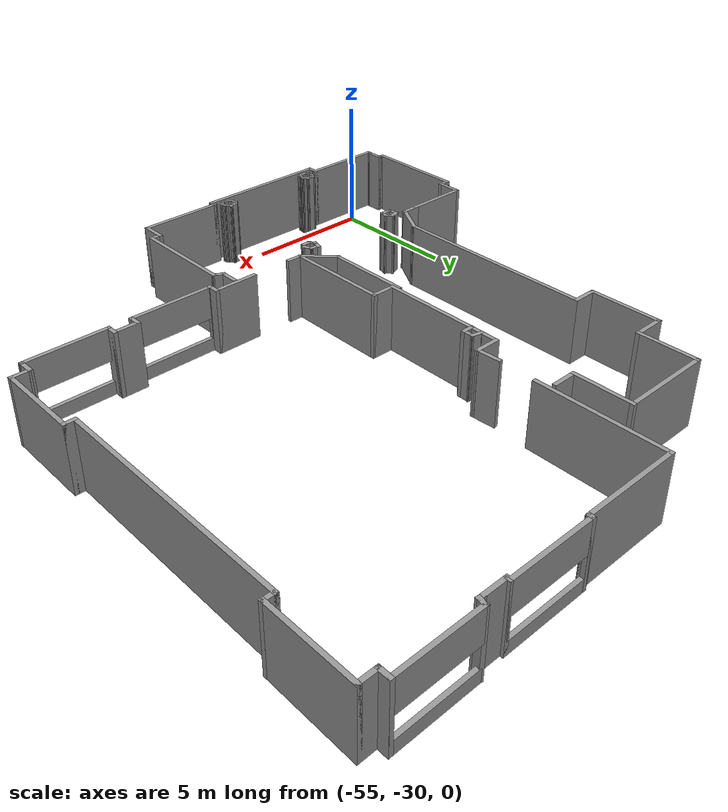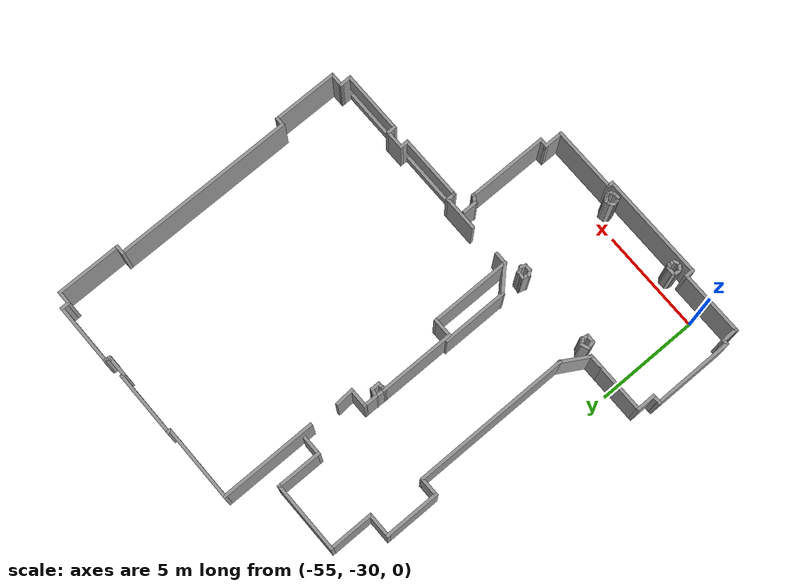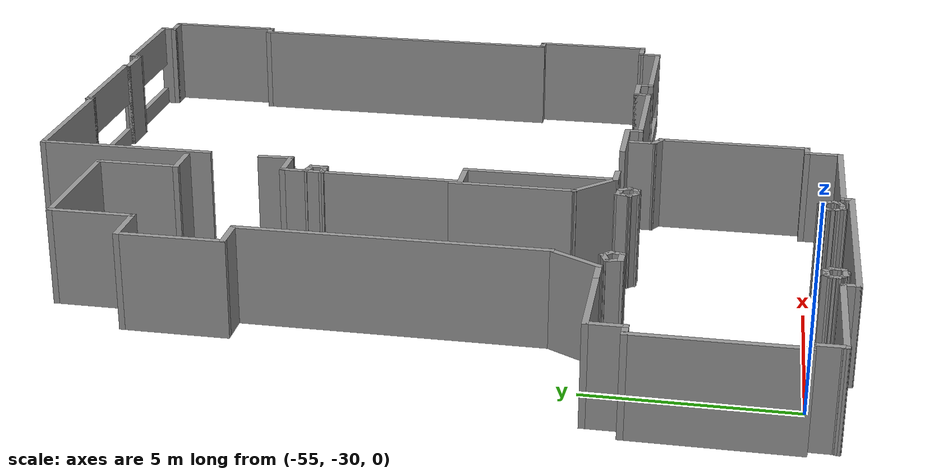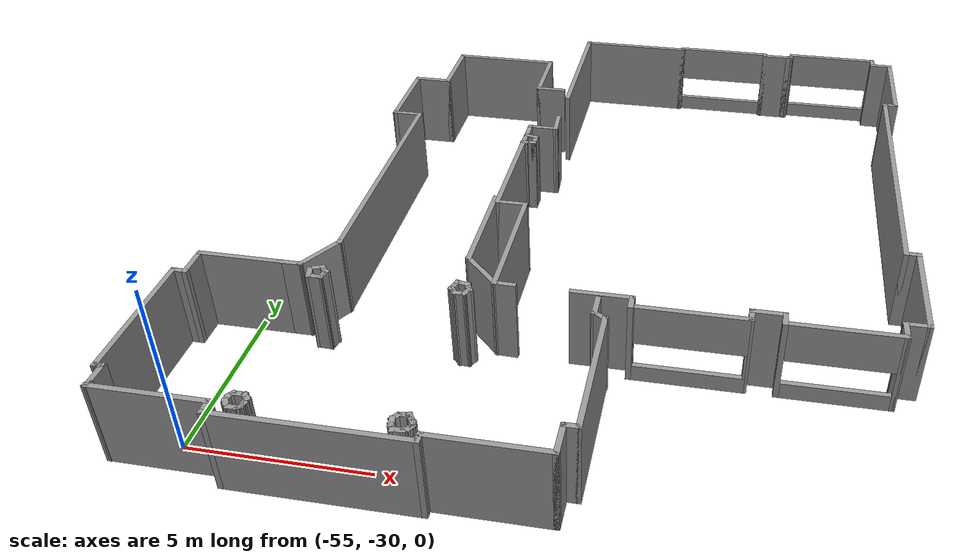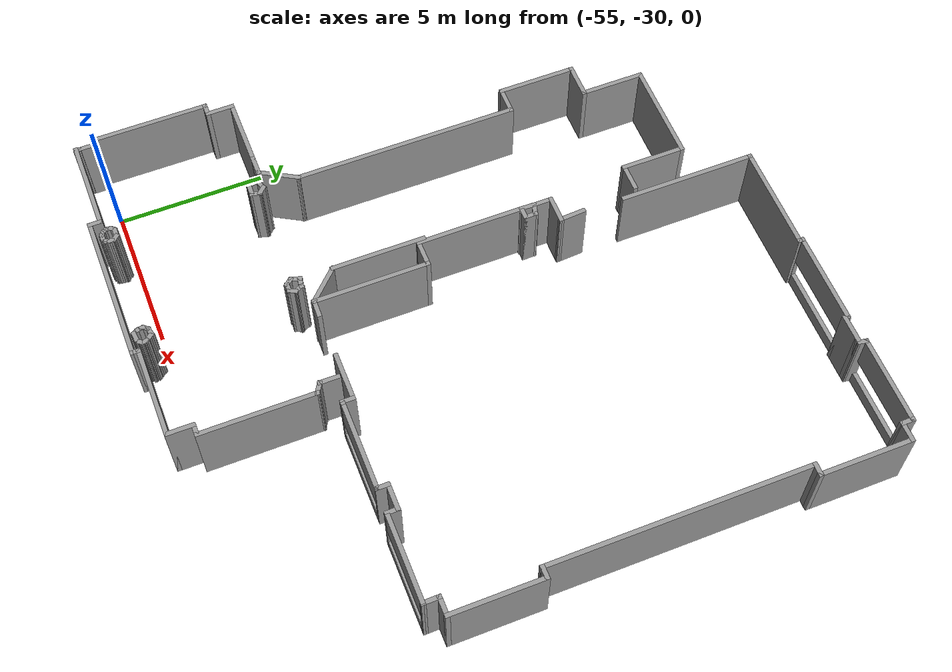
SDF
<?xml version='1.0'?>
<sdf version='1.7'>
  <model name='TD_n1'>
    <pose>-28.4203 -15.5404 0 0 -0 0</pose>
    <link name='Wall_10'>
      <collision name='Wall_10_Collision'>
        <geometry>
          <box>
            <size>3.25 0.15 2.5</size>
          </box>
        </geometry>
        <pose>0 0 1.25 0 -0 0</pose>
      </collision>
      <visual name='Wall_10_Visual'>
        <pose>0 0 1.25 0 -0 0</pose>
        <geometry>
          <box>
            <size>3.25 0.15 2.5</size>
          </box>
        </geometry>
        <material>
          <script>
            <uri>file://media/materials/scripts/gazebo.material</uri>
            <name>Gazebo/Grey</name>
          </script>
          <ambient>1 1 1 1</ambient>
        </material>
        <meta>
          <layer>0</layer>
        </meta>
      </visual>
      <pose>-8.40541 -7.90104 0 0 -0 -1.5708</pose>
    </link>
    <link name='Wall_100'>
      <collision name='Wall_100_Collision'>
        <geometry>
          <box>
            <size>0.417153 0.15 2.5</size>
          </box>
        </geometry>
        <pose>0 0 1.25 0 -0 0</pose>
      </collision>
      <visual name='Wall_100_Visual'>
        <pose>0 0 1.25 0 -0 0</pose>
        <geometry>
          <box>
            <size>0.417153 0.15 2.5</size>
          </box>
        </geometry>
        <material>
          <script>
            <uri>file://media/materials/scripts/gazebo.material</uri>
            <name>Gazebo/Grey</name>
          </script>
          <ambient>1 1 1 1</ambient>
        </material>
        <meta>
          <layer>0</layer>
        </meta>
      </visual>
      <pose>-24.2621 -10.0568 0 0 -0 -1.81236</pose>
    </link>
    <link name='Wall_101'>
      <collision name='Wall_101_Collision'>
        <geometry>
          <box>
            <size>0.488531 0.15 2.5</size>
          </box>
        </geometry>
        <pose>0 0 1.25 0 -0 0</pose>
      </collision>
      <visual name='Wall_101_Visual'>
        <pose>0 0 1.25 0 -0 0</pose>
        <geometry>
          <box>
            <size>0.488531 0.15 2.5</size>
          </box>
        </geometry>
        <material>
          <script>
            <uri>file://media/materials/scripts/gazebo.material</uri>
            <name>Gazebo/Grey</name>
          </script>
          <ambient>1 1 1 1</ambient>
        </material>
        <meta>
          <layer>0</layer>
        </meta>
      </visual>
      <pose>-24.4633 -10.1808 0 0 -0 3.10827</pose>
    </link>
    <link name='Wall_102'>
      <collision name='Wall_102_Collision'>
        <geometry>
          <box>
            <size>0.429005 0.15 2.5</size>
          </box>
        </geometry>
        <pose>0 0 1.25 0 -0 0</pose>
      </collision>
      <visual name='Wall_102_Visual'>
        <pose>0 0 1.25 0 -0 0</pose>
        <geometry>
          <box>
            <size>0.429005 0.15 2.5</size>
          </box>
        </geometry>
        <material>
          <script>
            <uri>file://media/materials/scripts/gazebo.material</uri>
            <name>Gazebo/Grey</name>
          </script>
          <ambient>1 1 1 1</ambient>
        </material>
        <meta>
          <layer>0</layer>
        </meta>
      </visual>
      <pose>-24.6663 -10.0398 0 0 -0 1.81577</pose>
    </link>
    <link name='Wall_104'>
      <collision name='Wall_104_Collision'>
        <geometry>
          <box>
            <size>0.437291 0.15 2.5</size>
          </box>
        </geometry>
        <pose>0 0 1.25 0 -0 0</pose>
      </collision>
      <visual name='Wall_104_Visual'>
        <pose>0 0 1.25 0 -0 0</pose>
        <geometry>
          <box>
            <size>0.437291 0.15 2.5</size>
          </box>
        </geometry>
        <material>
          <script>
            <uri>file://media/materials/scripts/gazebo.material</uri>
            <name>Gazebo/Grey</name>
          </script>
          <ambient>1 1 1 1</ambient>
        </material>
        <meta>
          <layer>0</layer>
        </meta>
      </visual>
      <pose>-20.4746 -9.7842 0 0 -0 -0.104877</pose>
    </link>
    <link name='Wall_105'>
      <collision name='Wall_105_Collision'>
        <geometry>
          <box>
            <size>0.408933 0.15 2.5</size>
          </box>
        </geometry>
        <pose>0 0 1.25 0 -0 0</pose>
      </collision>
      <visual name='Wall_105_Visual'>
        <pose>0 0 1.25 0 -0 0</pose>
        <geometry>
          <box>
            <size>0.408933 0.15 2.5</size>
          </box>
        </geometry>
        <material>
          <script>
            <uri>file://media/materials/scripts/gazebo.material</uri>
            <name>Gazebo/Grey</name>
          </script>
          <ambient>1 1 1 1</ambient>
        </material>
        <meta>
          <layer>0</layer>
        </meta>
      </visual>
      <pose>-20.2753 -9.91578 0 0 -0 -1.12014</pose>
    </link>
    <link name='Wall_106'>
      <collision name='Wall_106_Collision'>
        <geometry>
          <box>
            <size>0.355222 0.15 2.5</size>
          </box>
        </geometry>
        <pose>0 0 1.25 0 -0 0</pose>
      </collision>
      <visual name='Wall_106_Visual'>
        <pose>0 0 1.25 0 -0 0</pose>
        <geometry>
          <box>
            <size>0.355222 0.15 2.5</size>
          </box>
        </geometry>
        <material>
          <script>
            <uri>file://media/materials/scripts/gazebo.material</uri>
            <name>Gazebo/Grey</name>
          </script>
          <ambient>1 1 1 1</ambient>
        </material>
        <meta>
          <layer>0</layer>
        </meta>
      </visual>
      <pose>-20.2678 -10.1225 0 0 -0 -2.06722</pose>
    </link>
    <link name='Wall_107'>
      <collision name='Wall_107_Collision'>
        <geometry>
          <box>
            <size>0.3906 0.15 2.5</size>
          </box>
        </geometry>
        <pose>0 0 1.25 0 -0 0</pose>
      </collision>
      <visual name='Wall_107_Visual'>
        <pose>0 0 1.25 0 -0 0</pose>
        <geometry>
          <box>
            <size>0.3906 0.15 2.5</size>
          </box>
        </geometry>
        <material>
          <script>
            <uri>file://media/materials/scripts/gazebo.material</uri>
            <name>Gazebo/Grey</name>
          </script>
          <ambient>1 1 1 1</ambient>
        </material>
        <meta>
          <layer>0</layer>
        </meta>
      </visual>
      <pose>-20.437 -10.2128 0 0 -0 3.14159</pose>
    </link>
    <link name='Wall_108'>
      <collision name='Wall_108_Collision'>
        <geometry>
          <box>
            <size>0.368561 0.15 2.5</size>
          </box>
        </geometry>
        <pose>0 0 1.25 0 -0 0</pose>
      </collision>
      <visual name='Wall_108_Visual'>
        <pose>0 0 1.25 0 -0 0</pose>
        <geometry>
          <box>
            <size>0.368561 0.15 2.5</size>
          </box>
        </geometry>
        <material>
          <script>
            <uri>file://media/materials/scripts/gazebo.material</uri>
            <name>Gazebo/Grey</name>
          </script>
          <ambient>1 1 1 1</ambient>
        </material>
        <meta>
          <layer>0</layer>
        </meta>
      </visual>
      <pose>-20.6287 -10.1301 0 0 -0 2.28315</pose>
    </link>
    <link name='Wall_109'>
      <collision name='Wall_109_Collision'>
        <geometry>
          <box>
            <size>0.454671 0.15 2.5</size>
          </box>
        </geometry>
        <pose>0 0 1.25 0 -0 0</pose>
      </collision>
      <visual name='Wall_109_Visual'>
        <pose>0 0 1.25 0 -0 0</pose>
        <geometry>
          <box>
            <size>0.454671 0.15 2.5</size>
          </box>
        </geometry>
        <material>
          <script>
            <uri>file://media/materials/scripts/gazebo.material</uri>
            <name>Gazebo/Grey</name>
          </script>
          <ambient>1 1 1 1</ambient>
        </material>
        <meta>
          <layer>0</layer>
        </meta>
      </visual>
      <pose>-20.6588 -9.90075 0 0 -0 1.29589</pose>
    </link>
    <link name='Wall_111'>
      <collision name='Wall_111_Collision'>
        <geometry>
          <box>
            <size>0.38911 0.15 2.5</size>
          </box>
        </geometry>
        <pose>0 0 1.25 0 -0 0</pose>
      </collision>
      <visual name='Wall_111_Visual'>
        <pose>0 0 1.25 0 -0 0</pose>
        <geometry>
          <box>
            <size>0.38911 0.15 2.5</size>
          </box>
        </geometry>
        <material>
          <script>
            <uri>file://media/materials/scripts/gazebo.material</uri>
            <name>Gazebo/Grey</name>
          </script>
          <ambient>1 1 1 1</ambient>
        </material>
        <meta>
          <layer>0</layer>
        </meta>
      </visual>
      <pose>-24.4695 -14.7595 0 0 -0 0</pose>
    </link>
    <link name='Wall_112'>
      <collision name='Wall_112_Collision'>
        <geometry>
          <box>
            <size>0.315269 0.15 2.5</size>
          </box>
        </geometry>
        <pose>0 0 1.25 0 -0 0</pose>
      </collision>
      <visual name='Wall_112_Visual'>
        <pose>0 0 1.25 0 -0 0</pose>
        <geometry>
          <box>
            <size>0.315269 0.15 2.5</size>
          </box>
        </geometry>
        <material>
          <script>
            <uri>file://media/materials/scripts/gazebo.material</uri>
            <name>Gazebo/Grey</name>
          </script>
          <ambient>1 1 1 1</ambient>
        </material>
        <meta>
          <layer>0</layer>
        </meta>
      </visual>
      <pose>-24.293 -14.8191 0 0 -0 -0.806672</pose>
    </link>
    <link name='Wall_113'>
      <collision name='Wall_113_Collision'>
        <geometry>
          <box>
            <size>0.299897 0.15 2.5</size>
          </box>
        </geometry>
        <pose>0 0 1.25 0 -0 0</pose>
      </collision>
      <visual name='Wall_113_Visual'>
        <pose>0 0 1.25 0 -0 0</pose>
        <geometry>
          <box>
            <size>0.299897 0.15 2.5</size>
          </box>
        </geometry>
        <material>
          <script>
            <uri>file://media/materials/scripts/gazebo.material</uri>
            <name>Gazebo/Grey</name>
          </script>
          <ambient>1 1 1 1</ambient>
        </material>
        <meta>
          <layer>0</layer>
        </meta>
      </visual>
      <pose>-24.2383 -14.9534 0 0 -0 -1.60412</pose>
    </link>
    <link name='Wall_114'>
      <collision name='Wall_114_Collision'>
        <geometry>
          <box>
            <size>0.279075 0.15 2.5</size>
          </box>
        </geometry>
        <pose>0 0 1.25 0 -0 0</pose>
      </collision>
      <visual name='Wall_114_Visual'>
        <pose>0 0 1.25 0 -0 0</pose>
        <geometry>
          <box>
            <size>0.279075 0.15 2.5</size>
          </box>
        </geometry>
        <material>
          <script>
            <uri>file://media/materials/scripts/gazebo.material</uri>
            <name>Gazebo/Grey</name>
          </script>
          <ambient>1 1 1 1</ambient>
        </material>
        <meta>
          <layer>0</layer>
        </meta>
      </visual>
      <pose>-24.2582 -15.0901 0 0 -0 -1.8438</pose>
    </link>
    <link name='Wall_115'>
      <collision name='Wall_115_Collision'>
        <geometry>
          <box>
            <size>0.281258 0.15 2.5</size>
          </box>
        </geometry>
        <pose>0 0 1.25 0 -0 0</pose>
      </collision>
      <visual name='Wall_115_Visual'>
        <pose>0 0 1.25 0 -0 0</pose>
        <geometry>
          <box>
            <size>0.281258 0.15 2.5</size>
          </box>
        </geometry>
        <material>
          <script>
            <uri>file://media/materials/scripts/gazebo.material</uri>
            <name>Gazebo/Grey</name>
          </script>
          <ambient>1 1 1 1</ambient>
        </material>
        <meta>
          <layer>0</layer>
        </meta>
      </visual>
      <pose>-24.3353 -15.1796 0 0 -0 -2.71183</pose>
    </link>
    <link name='Wall_116'>
      <collision name='Wall_116_Collision'>
        <geometry>
          <box>
            <size>0.304445 0.15 2.5</size>
          </box>
        </geometry>
        <pose>0 0 1.25 0 -0 0</pose>
      </collision>
      <visual name='Wall_116_Visual'>
        <pose>0 0 1.25 0 -0 0</pose>
        <geometry>
          <box>
            <size>0.304445 0.15 2.5</size>
          </box>
        </geometry>
        <material>
          <script>
            <uri>file://media/materials/scripts/gazebo.material</uri>
            <name>Gazebo/Grey</name>
          </script>
          <ambient>1 1 1 1</ambient>
        </material>
        <meta>
          <layer>0</layer>
        </meta>
      </visual>
      <pose>-24.472 -15.202 0 0 -0 3.07717</pose>
    </link>
    <link name='Wall_117'>
      <collision name='Wall_117_Collision'>
        <geometry>
          <box>
            <size>0.281258 0.15 2.5</size>
          </box>
        </geometry>
        <pose>0 0 1.25 0 -0 0</pose>
      </collision>
      <visual name='Wall_117_Visual'>
        <pose>0 0 1.25 0 -0 0</pose>
        <geometry>
          <box>
            <size>0.281258 0.15 2.5</size>
          </box>
        </geometry>
        <material>
          <script>
            <uri>file://media/materials/scripts/gazebo.material</uri>
            <name>Gazebo/Grey</name>
          </script>
          <ambient>1 1 1 1</ambient>
        </material>
        <meta>
          <layer>0</layer>
        </meta>
      </visual>
      <pose>-24.6013 -15.1572 0 0 -0 2.49052</pose>
    </link>
    <link name='Wall_118'>
      <collision name='Wall_118_Collision'>
        <geometry>
          <box>
            <size>0.267863 0.15 2.5</size>
          </box>
        </geometry>
        <pose>0 0 1.25 0 -0 0</pose>
      </collision>
      <visual name='Wall_118_Visual'>
        <pose>0 0 1.25 0 -0 0</pose>
        <geometry>
          <box>
            <size>0.267863 0.15 2.5</size>
          </box>
        </geometry>
        <material>
          <script>
            <uri>file://media/materials/scripts/gazebo.material</uri>
            <name>Gazebo/Grey</name>
          </script>
          <ambient>1 1 1 1</ambient>
        </material>
        <meta>
          <layer>0</layer>
        </meta>
      </visual>
      <pose>-24.6808 -15.0652 0 0 -0 2.05331</pose>
    </link>
    <link name='Wall_119'>
      <collision name='Wall_119_Collision'>
        <geometry>
          <box>
            <size>0.299484 0.15 2.5</size>
          </box>
        </geometry>
        <pose>0 0 1.25 0 -0 0</pose>
      </collision>
      <visual name='Wall_119_Visual'>
        <pose>0 0 1.25 0 -0 0</pose>
        <geometry>
          <box>
            <size>0.299484 0.15 2.5</size>
          </box>
        </geometry>
        <material>
          <script>
            <uri>file://media/materials/scripts/gazebo.material</uri>
            <name>Gazebo/Grey</name>
          </script>
          <ambient>1 1 1 1</ambient>
        </material>
        <meta>
          <layer>0</layer>
        </meta>
      </visual>
      <pose>-24.7032 -14.9385 0 0 -0 1.50423</pose>
    </link>
    <link name='Wall_120'>
      <collision name='Wall_120_Collision'>
        <geometry>
          <box>
            <size>0.271376 0.15 2.5</size>
          </box>
        </geometry>
        <pose>0 0 1.25 0 -0 0</pose>
      </collision>
      <visual name='Wall_120_Visual'>
        <pose>0 0 1.25 0 -0 0</pose>
        <geometry>
          <box>
            <size>0.271376 0.15 2.5</size>
          </box>
        </geometry>
        <material>
          <script>
            <uri>file://media/materials/scripts/gazebo.material</uri>
            <name>Gazebo/Grey</name>
          </script>
          <ambient>1 1 1 1</ambient>
        </material>
        <meta>
          <layer>0</layer>
        </meta>
      </visual>
      <pose>-24.6634 -14.8142 0 0 -0 0.96007</pose>
    </link>
    <link name='Wall_122'>
      <collision name='Wall_122_Collision'>
        <geometry>
          <box>
            <size>0.340556 0.15 2.5</size>
          </box>
        </geometry>
        <pose>0 0 1.25 0 -0 0</pose>
      </collision>
      <visual name='Wall_122_Visual'>
        <pose>0 0 1.25 0 -0 0</pose>
        <geometry>
          <box>
            <size>0.340556 0.15 2.5</size>
          </box>
        </geometry>
        <material>
          <script>
            <uri>file://media/materials/scripts/gazebo.material</uri>
            <name>Gazebo/Grey</name>
          </script>
          <ambient>1 1 1 1</ambient>
        </material>
        <meta>
          <layer>0</layer>
        </meta>
      </visual>
      <pose>-20.4822 -14.7371 0 0 -0 0.130827</pose>
    </link>
    <link name='Wall_123'>
      <collision name='Wall_123_Collision'>
        <geometry>
          <box>
            <size>0.252496 0.15 2.5</size>
          </box>
        </geometry>
        <pose>0 0 1.25 0 -0 0</pose>
      </collision>
      <visual name='Wall_123_Visual'>
        <pose>0 0 1.25 0 -0 0</pose>
        <geometry>
          <box>
            <size>0.252496 0.15 2.5</size>
          </box>
        </geometry>
        <material>
          <script>
            <uri>file://media/materials/scripts/gazebo.material</uri>
            <name>Gazebo/Grey</name>
          </script>
          <ambient>1 1 1 1</ambient>
        </material>
        <meta>
          <layer>0</layer>
        </meta>
      </visual>
      <pose>-20.3554 -14.7645 0 0 -0 -0.88848</pose>
    </link>
    <link name='Wall_124'>
      <collision name='Wall_124_Collision'>
        <geometry>
          <box>
            <size>0.306117 0.15 2.5</size>
          </box>
        </geometry>
        <pose>0 0 1.25 0 -0 0</pose>
      </collision>
      <visual name='Wall_124_Visual'>
        <pose>0 0 1.25 0 -0 0</pose>
        <geometry>
          <box>
            <size>0.306117 0.15 2.5</size>
          </box>
        </geometry>
        <material>
          <script>
            <uri>file://media/materials/scripts/gazebo.material</uri>
            <name>Gazebo/Grey</name>
          </script>
          <ambient>1 1 1 1</ambient>
        </material>
        <meta>
          <layer>0</layer>
        </meta>
      </visual>
      <pose>-20.2758 -14.8664 0 0 -0 -0.920926</pose>
    </link>
    <link name='Wall_125'>
      <collision name='Wall_125_Collision'>
        <geometry>
          <box>
            <size>0.271884 0.15 2.5</size>
          </box>
        </geometry>
        <pose>0 0 1.25 0 -0 0</pose>
      </collision>
      <visual name='Wall_125_Visual'>
        <pose>0 0 1.25 0 -0 0</pose>
        <geometry>
          <box>
            <size>0.271884 0.15 2.5</size>
          </box>
        </geometry>
        <material>
          <script>
            <uri>file://media/materials/scripts/gazebo.material</uri>
            <name>Gazebo/Grey</name>
          </script>
          <ambient>1 1 1 1</ambient>
        </material>
        <meta>
          <layer>0</layer>
        </meta>
      </visual>
      <pose>-20.2162 -14.9882 0 0 -0 -1.3654</pose>
    </link>
    <link name='Wall_126'>
      <collision name='Wall_126_Collision'>
        <geometry>
          <box>
            <size>0.265961 0.15 2.5</size>
          </box>
        </geometry>
        <pose>0 0 1.25 0 -0 0</pose>
      </collision>
      <visual name='Wall_126_Visual'>
        <pose>0 0 1.25 0 -0 0</pose>
        <geometry>
          <box>
            <size>0.265961 0.15 2.5</size>
          </box>
        </geometry>
        <material>
          <script>
            <uri>file://media/materials/scripts/gazebo.material</uri>
            <name>Gazebo/Grey</name>
          </script>
          <ambient>1 1 1 1</ambient>
        </material>
        <meta>
          <layer>0</layer>
        </meta>
      </visual>
      <pose>-20.2336 -15.0976 0 0 -0 -2.11122</pose>
    </link>
    <link name='Wall_127'>
      <collision name='Wall_127_Collision'>
        <geometry>
          <box>
            <size>0.281353 0.15 2.5</size>
          </box>
        </geometry>
        <pose>0 0 1.25 0 -0 0</pose>
      </collision>
      <visual name='Wall_127_Visual'>
        <pose>0 0 1.25 0 -0 0</pose>
        <geometry>
          <box>
            <size>0.281353 0.15 2.5</size>
          </box>
        </geometry>
        <material>
          <script>
            <uri>file://media/materials/scripts/gazebo.material</uri>
            <name>Gazebo/Grey</name>
          </script>
          <ambient>1 1 1 1</ambient>
        </material>
        <meta>
          <layer>0</layer>
        </meta>
      </visual>
      <pose>-20.3206 -15.1796 0 0 -0 -2.62714</pose>
    </link>
    <link name='Wall_128'>
      <collision name='Wall_128_Collision'>
        <geometry>
          <box>
            <size>0.385569 0.15 2.5</size>
          </box>
        </geometry>
        <pose>0 0 1.25 0 -0 0</pose>
      </collision>
      <visual name='Wall_128_Visual'>
        <pose>0 0 1.25 0 -0 0</pose>
        <geometry>
          <box>
            <size>0.385569 0.15 2.5</size>
          </box>
        </geometry>
        <material>
          <script>
            <uri>file://media/materials/scripts/gazebo.material</uri>
            <name>Gazebo/Grey</name>
          </script>
          <ambient>1 1 1 1</ambient>
        </material>
        <meta>
          <layer>0</layer>
        </meta>
      </visual>
      <pose>-20.4946 -15.2243 0 0 -0 -3.03561</pose>
    </link>
    <link name='Wall_129'>
      <collision name='Wall_129_Collision'>
        <geometry>
          <box>
            <size>0.325779 0.15 2.5</size>
          </box>
        </geometry>
        <pose>0 0 1.25 0 -0 0</pose>
      </collision>
      <visual name='Wall_129_Visual'>
        <pose>0 0 1.25 0 -0 0</pose>
        <geometry>
          <box>
            <size>0.325779 0.15 2.5</size>
          </box>
        </geometry>
        <material>
          <script>
            <uri>file://media/materials/scripts/gazebo.material</uri>
            <name>Gazebo/Grey</name>
          </script>
          <ambient>1 1 1 1</ambient>
        </material>
        <meta>
          <layer>0</layer>
        </meta>
      </visual>
      <pose>-20.6537 -15.1597 0 0 -0 2.0724</pose>
    </link>
    <link name='Wall_130'>
      <collision name='Wall_130_Collision'>
        <geometry>
          <box>
            <size>0.330702 0.15 2.5</size>
          </box>
        </geometry>
        <pose>0 0 1.25 0 -0 0</pose>
      </collision>
      <visual name='Wall_130_Visual'>
        <pose>0 0 1.25 0 -0 0</pose>
        <geometry>
          <box>
            <size>0.330702 0.15 2.5</size>
          </box>
        </geometry>
        <material>
          <script>
            <uri>file://media/materials/scripts/gazebo.material</uri>
            <name>Gazebo/Grey</name>
          </script>
          <ambient>1 1 1 1</ambient>
        </material>
        <meta>
          <layer>0</layer>
        </meta>
      </visual>
      <pose>-20.7084 -14.9932 0 0 -0 1.7088</pose>
    </link>
    <link name='Wall_131'>
      <collision name='Wall_131_Collision'>
        <geometry>
          <box>
            <size>0.300309 0.15 2.5</size>
          </box>
        </geometry>
        <pose>0 0 1.25 0 -0 0</pose>
      </collision>
      <visual name='Wall_131_Visual'>
        <pose>0 0 1.25 0 -0 0</pose>
        <geometry>
          <box>
            <size>0.300309 0.15 2.5</size>
          </box>
        </geometry>
        <material>
          <script>
            <uri>file://media/materials/scripts/gazebo.material</uri>
            <name>Gazebo/Grey</name>
          </script>
          <ambient>1 1 1 1</ambient>
        </material>
        <meta>
          <layer>0</layer>
        </meta>
      </visual>
      <pose>-20.6786 -14.8415 0 0 -0 0.97362</pose>
    </link>
    <link name='Wall_15'>
      <collision name='Wall_15_Collision'>
        <geometry>
          <box>
            <size>0.75 0.15 2.5</size>
          </box>
        </geometry>
        <pose>0 0 1.25 0 -0 0</pose>
      </collision>
      <visual name='Wall_15_Visual'>
        <pose>0 0 1.25 0 -0 0</pose>
        <geometry>
          <box>
            <size>0.75 0.15 2.5</size>
          </box>
        </geometry>
        <material>
          <script>
            <uri>file://media/materials/scripts/gazebo.material</uri>
            <name>Gazebo/Grey</name>
          </script>
          <ambient>1 1 1 1</ambient>
        </material>
        <meta>
          <layer>0</layer>
        </meta>
      </visual>
      <pose>-8.70541 -9.45104 0 0 -0 0</pose>
    </link>
    <link name='Wall_17'>
      <collision name='Wall_17_Collision'>
        <geometry>
          <box>
            <size>0.658615 0.15 2.5</size>
          </box>
        </geometry>
        <pose>0 0 1.25 0 -0 0</pose>
      </collision>
      <visual name='Wall_17_Visual'>
        <pose>0 0 1.25 0 -0 0</pose>
        <geometry>
          <box>
            <size>0.658615 0.15 2.5</size>
          </box>
        </geometry>
        <material>
          <script>
            <uri>file://media/materials/scripts/gazebo.material</uri>
            <name>Gazebo/Grey</name>
          </script>
          <ambient>1 1 1 1</ambient>
        </material>
        <meta>
          <layer>0</layer>
        </meta>
      </visual>
      <pose>-9.00103 -9.70531 0 0 -0 1.588</pose>
    </link>
    <link name='Wall_19'>
      <pose>-10.4967 -9.95958 0 0 -0 3.14159</pose>
      <visual name='Wall_19_Visual_0'>
        <pose>-1.55302 0 1.25 0 -0 0</pose>
        <geometry>
          <box>
            <size>0.043952 0.15 2.5</size>
          </box>
        </geometry>
        <material>
          <script>
            <uri>file://media/materials/scripts/gazebo.material</uri>
            <name>Gazebo/Grey</name>
          </script>
          <ambient>1 1 1 1</ambient>
        </material>
        <meta>
          <layer>0</layer>
        </meta>
      </visual>
      <collision name='Wall_19_Collision_0'>
        <geometry>
          <box>
            <size>0.043952 0.15 2.5</size>
          </box>
        </geometry>
        <pose>-1.55302 0 1.25 0 -0 0</pose>
      </collision>
      <visual name='Wall_19_Visual_1'>
        <pose>0.021976 0 0.25 0 -0 0</pose>
        <geometry>
          <box>
            <size>3.10605 0.15 0.5</size>
          </box>
        </geometry>
        <material>
          <script>
            <uri>file://media/materials/scripts/gazebo.material</uri>
            <name>Gazebo/Grey</name>
          </script>
          <ambient>1 1 1 1</ambient>
        </material>
        <meta>
          <layer>0</layer>
        </meta>
      </visual>
      <collision name='Wall_19_Collision_1'>
        <geometry>
          <box>
            <size>3.10605 0.15 0.5</size>
          </box>
        </geometry>
        <pose>0.021976 0 0.25 0 -0 0</pose>
      </collision>
      <visual name='Wall_19_Visual_2'>
        <pose>1.52198 0 1.5 0 -0 0</pose>
        <geometry>
          <box>
            <size>0.106048 0.15 2</size>
          </box>
        </geometry>
        <material>
          <script>
            <uri>file://media/materials/scripts/gazebo.material</uri>
            <name>Gazebo/Grey</name>
          </script>
          <ambient>1 1 1 1</ambient>
        </material>
        <meta>
          <layer>0</layer>
        </meta>
      </visual>
      <collision name='Wall_19_Collision_2'>
        <geometry>
          <box>
            <size>0.106048 0.15 2</size>
          </box>
        </geometry>
        <pose>1.52198 0 1.5 0 -0 0</pose>
      </collision>
      <visual name='Wall_19_Visual_3'>
        <pose>-0.031048 0 1.9 0 -0 0</pose>
        <geometry>
          <box>
            <size>3 0.15 1.2</size>
          </box>
        </geometry>
        <material>
          <script>
            <uri>file://media/materials/scripts/gazebo.material</uri>
            <name>Gazebo/Grey</name>
          </script>
          <ambient>1 1 1 1</ambient>
        </material>
        <meta>
          <layer>0</layer>
        </meta>
      </visual>
      <collision name='Wall_19_Collision_3'>
        <geometry>
          <box>
            <size>3 0.15 1.2</size>
          </box>
        </geometry>
        <pose>-0.031048 0 1.9 0 -0 0</pose>
      </collision>
    </link>
    <link name='Wall_2'>
      <pose>-10.4734 5.94896 0 0 -0 0</pose>
      <visual name='Wall_2_Visual_0'>
        <pose>-1.52604 0 1.25 0 -0 0</pose>
        <geometry>
          <box>
            <size>0.033869 0.15 2.5</size>
          </box>
        </geometry>
        <material>
          <script>
            <uri>file://media/materials/scripts/gazebo.material</uri>
            <name>Gazebo/Grey</name>
          </script>
          <ambient>1 1 1 1</ambient>
        </material>
        <meta>
          <layer>0</layer>
        </meta>
      </visual>
      <collision name='Wall_2_Collision_0'>
        <geometry>
          <box>
            <size>0.033869 0.15 2.5</size>
          </box>
        </geometry>
        <pose>-1.52604 0 1.25 0 -0 0</pose>
      </collision>
      <visual name='Wall_2_Visual_1'>
        <pose>0.016935 0 0.25 0 -0 0</pose>
        <geometry>
          <box>
            <size>3.05208 0.15 0.5</size>
          </box>
        </geometry>
        <material>
          <script>
            <uri>file://media/materials/scripts/gazebo.material</uri>
            <name>Gazebo/Grey</name>
          </script>
          <ambient>1 1 1 1</ambient>
        </material>
        <meta>
          <layer>0</layer>
        </meta>
      </visual>
      <collision name='Wall_2_Collision_1'>
        <geometry>
          <box>
            <size>3.05208 0.15 0.5</size>
          </box>
        </geometry>
        <pose>0.016935 0 0.25 0 -0 0</pose>
      </collision>
      <visual name='Wall_2_Visual_2'>
        <pose>1.51693 0 1.5 0 -0 0</pose>
        <geometry>
          <box>
            <size>0.052081 0.15 2</size>
          </box>
        </geometry>
        <material>
          <script>
            <uri>file://media/materials/scripts/gazebo.material</uri>
            <name>Gazebo/Grey</name>
          </script>
          <ambient>1 1 1 1</ambient>
        </material>
        <meta>
          <layer>0</layer>
        </meta>
      </visual>
      <collision name='Wall_2_Collision_2'>
        <geometry>
          <box>
            <size>0.052081 0.15 2</size>
          </box>
        </geometry>
        <pose>1.51693 0 1.5 0 -0 0</pose>
      </collision>
      <visual name='Wall_2_Visual_3'>
        <pose>-0.009106 0 1.9 0 -0 0</pose>
        <geometry>
          <box>
            <size>3 0.15 1.2</size>
          </box>
        </geometry>
        <material>
          <script>
            <uri>file://media/materials/scripts/gazebo.material</uri>
            <name>Gazebo/Grey</name>
          </script>
          <ambient>1 1 1 1</ambient>
        </material>
        <meta>
          <layer>0</layer>
        </meta>
      </visual>
      <collision name='Wall_2_Collision_3'>
        <geometry>
          <box>
            <size>3 0.15 1.2</size>
          </box>
        </geometry>
        <pose>-0.009106 0 1.9 0 -0 0</pose>
      </collision>
    </link>
    <link name='Wall_21'>
      <collision name='Wall_21_Collision'>
        <geometry>
          <box>
            <size>0.5 0.15 2.5</size>
          </box>
        </geometry>
        <pose>0 0 1.25 0 -0 0</pose>
      </collision>
      <visual name='Wall_21_Visual'>
        <pose>0 0 1.25 0 -0 0</pose>
        <geometry>
          <box>
            <size>0.5 0.15 2.5</size>
          </box>
        </geometry>
        <material>
          <script>
            <uri>file://media/materials/scripts/gazebo.material</uri>
            <name>Gazebo/Grey</name>
          </script>
          <ambient>1 1 1 1</ambient>
        </material>
        <meta>
          <layer>0</layer>
        </meta>
      </visual>
      <pose>-11.9967 -9.78458 0 0 -0 1.5708</pose>
    </link>
    <link name='Wall_22'>
      <collision name='Wall_22_Collision'>
        <geometry>
          <box>
            <size>1 0.15 2.5</size>
          </box>
        </geometry>
        <pose>0 0 1.25 0 -0 0</pose>
      </collision>
      <visual name='Wall_22_Visual'>
        <pose>0 0 1.25 0 -0 0</pose>
        <geometry>
          <box>
            <size>1 0.15 2.5</size>
          </box>
        </geometry>
        <material>
          <script>
            <uri>file://media/materials/scripts/gazebo.material</uri>
            <name>Gazebo/Grey</name>
          </script>
          <ambient>1 1 1 1</ambient>
        </material>
        <meta>
          <layer>0</layer>
        </meta>
      </visual>
      <pose>-12.4217 -9.60958 0 0 -0 3.14159</pose>
    </link>
    <link name='Wall_23'>
      <collision name='Wall_23_Collision'>
        <geometry>
          <box>
            <size>0.5 0.15 2.5</size>
          </box>
        </geometry>
        <pose>0 0 1.25 0 -0 0</pose>
      </collision>
      <visual name='Wall_23_Visual'>
        <pose>0 0 1.25 0 -0 0</pose>
        <geometry>
          <box>
            <size>0.5 0.15 2.5</size>
          </box>
        </geometry>
        <material>
          <script>
            <uri>file://media/materials/scripts/gazebo.material</uri>
            <name>Gazebo/Grey</name>
          </script>
          <ambient>1 1 1 1</ambient>
        </material>
        <meta>
          <layer>0</layer>
        </meta>
      </visual>
      <pose>-12.8467 -9.78458 0 0 -0 -1.5708</pose>
    </link>
    <link name='Wall_24'>
      <pose>-14.3967 -9.95958 0 0 -0 3.14159</pose>
      <visual name='Wall_24_Visual_0'>
        <pose>-1.58877 0 1.25 0 -0 0</pose>
        <geometry>
          <box>
            <size>0.07246 0.15 2.5</size>
          </box>
        </geometry>
        <material>
          <script>
            <uri>file://media/materials/scripts/gazebo.material</uri>
            <name>Gazebo/Grey</name>
          </script>
          <ambient>1 1 1 1</ambient>
        </material>
        <meta>
          <layer>0</layer>
        </meta>
      </visual>
      <collision name='Wall_24_Collision_0'>
        <geometry>
          <box>
            <size>0.07246 0.15 2.5</size>
          </box>
        </geometry>
        <pose>-1.58877 0 1.25 0 -0 0</pose>
      </collision>
      <visual name='Wall_24_Visual_1'>
        <pose>0.03623 0 0.25 0 -0 0</pose>
        <geometry>
          <box>
            <size>3.17754 0.15 0.5</size>
          </box>
        </geometry>
        <material>
          <script>
            <uri>file://media/materials/scripts/gazebo.material</uri>
            <name>Gazebo/Grey</name>
          </script>
          <ambient>1 1 1 1</ambient>
        </material>
        <meta>
          <layer>0</layer>
        </meta>
      </visual>
      <collision name='Wall_24_Collision_1'>
        <geometry>
          <box>
            <size>3.17754 0.15 0.5</size>
          </box>
        </geometry>
        <pose>0.03623 0 0.25 0 -0 0</pose>
      </collision>
      <visual name='Wall_24_Visual_2'>
        <pose>1.53623 0 1.5 0 -0 0</pose>
        <geometry>
          <box>
            <size>0.17754 0.15 2</size>
          </box>
        </geometry>
        <material>
          <script>
            <uri>file://media/materials/scripts/gazebo.material</uri>
            <name>Gazebo/Grey</name>
          </script>
          <ambient>1 1 1 1</ambient>
        </material>
        <meta>
          <layer>0</layer>
        </meta>
      </visual>
      <collision name='Wall_24_Collision_2'>
        <geometry>
          <box>
            <size>0.17754 0.15 2</size>
          </box>
        </geometry>
        <pose>1.53623 0 1.5 0 -0 0</pose>
      </collision>
      <visual name='Wall_24_Visual_3'>
        <pose>-0.05254 0 1.9 0 -0 0</pose>
        <geometry>
          <box>
            <size>3 0.15 1.2</size>
          </box>
        </geometry>
        <material>
          <script>
            <uri>file://media/materials/scripts/gazebo.material</uri>
            <name>Gazebo/Grey</name>
          </script>
          <ambient>1 1 1 1</ambient>
        </material>
        <meta>
          <layer>0</layer>
        </meta>
      </visual>
      <collision name='Wall_24_Collision_3'>
        <geometry>
          <box>
            <size>3 0.15 1.2</size>
          </box>
        </geometry>
        <pose>-0.05254 0 1.9 0 -0 0</pose>
      </collision>
    </link>
    <link name='Wall_25'>
      <collision name='Wall_25_Collision'>
        <geometry>
          <box>
            <size>0.5 0.15 2.5</size>
          </box>
        </geometry>
        <pose>0 0 1.25 0 -0 0</pose>
      </collision>
      <visual name='Wall_25_Visual'>
        <pose>0 0 1.25 0 -0 0</pose>
        <geometry>
          <box>
            <size>0.5 0.15 2.5</size>
          </box>
        </geometry>
        <material>
          <script>
            <uri>file://media/materials/scripts/gazebo.material</uri>
            <name>Gazebo/Grey</name>
          </script>
          <ambient>1 1 1 1</ambient>
        </material>
        <meta>
          <layer>0</layer>
        </meta>
      </visual>
      <pose>-15.9467 -9.78458 0 0 -0 1.5708</pose>
    </link>
    <link name='Wall_26'>
      <collision name='Wall_26_Collision'>
        <geometry>
          <box>
            <size>1.75 0.15 2.5</size>
          </box>
        </geometry>
        <pose>0 0 1.25 0 -0 0</pose>
      </collision>
      <visual name='Wall_26_Visual'>
        <pose>0 0 1.25 0 -0 0</pose>
        <geometry>
          <box>
            <size>1.75 0.15 2.5</size>
          </box>
        </geometry>
        <material>
          <script>
            <uri>file://media/materials/scripts/gazebo.material</uri>
            <name>Gazebo/Grey</name>
          </script>
          <ambient>1 1 1 1</ambient>
        </material>
        <meta>
          <layer>0</layer>
        </meta>
      </visual>
      <pose>-16.7467 -9.60958 0 0 -0 3.14159</pose>
    </link>
    <link name='Wall_28'>
      <collision name='Wall_28_Collision'>
        <geometry>
          <box>
            <size>4 0.15 2.5</size>
          </box>
        </geometry>
        <pose>0 0 1.25 0 -0 0</pose>
      </collision>
      <visual name='Wall_28_Visual'>
        <pose>0 0 1.25 0 -0 0</pose>
        <geometry>
          <box>
            <size>4 0.15 2.5</size>
          </box>
        </geometry>
        <material>
          <script>
            <uri>file://media/materials/scripts/gazebo.material</uri>
            <name>Gazebo/Grey</name>
          </script>
          <ambient>1 1 1 1</ambient>
        </material>
        <meta>
          <layer>0</layer>
        </meta>
      </visual>
      <pose>-19.6467 -7.68458 0 0 -0 1.5708</pose>
    </link>
    <link name='Wall_29'>
      <collision name='Wall_29_Collision'>
        <geometry>
          <box>
            <size>1 0.15 2.5</size>
          </box>
        </geometry>
        <pose>0 0 1.25 0 -0 0</pose>
      </collision>
      <visual name='Wall_29_Visual'>
        <pose>0 0 1.25 0 -0 0</pose>
        <geometry>
          <box>
            <size>1 0.15 2.5</size>
          </box>
        </geometry>
        <material>
          <script>
            <uri>file://media/materials/scripts/gazebo.material</uri>
            <name>Gazebo/Grey</name>
          </script>
          <ambient>1 1 1 1</ambient>
        </material>
        <meta>
          <layer>0</layer>
        </meta>
      </visual>
      <pose>-20.0717 -5.75958 0 0 -0 3.14159</pose>
    </link>
    <link name='Wall_3'>
      <collision name='Wall_3_Collision'>
        <geometry>
          <box>
            <size>0.5 0.15 2.5</size>
          </box>
        </geometry>
        <pose>0 0 1.25 0 -0 0</pose>
      </collision>
      <visual name='Wall_3_Visual'>
        <pose>0 0 1.25 0 -0 0</pose>
        <geometry>
          <box>
            <size>0.5 0.15 2.5</size>
          </box>
        </geometry>
        <material>
          <script>
            <uri>file://media/materials/scripts/gazebo.material</uri>
            <name>Gazebo/Grey</name>
          </script>
          <ambient>1 1 1 1</ambient>
        </material>
        <meta>
          <layer>0</layer>
        </meta>
      </visual>
      <pose>-9.0054 5.77396 0 0 -0 -1.5708</pose>
    </link>
    <link name='Wall_31'>
      <collision name='Wall_31_Collision'>
        <geometry>
          <box>
            <size>3.75 0.15 2.5</size>
          </box>
        </geometry>
        <pose>0 0 1.25 0 -0 0</pose>
      </collision>
      <visual name='Wall_31_Visual'>
        <pose>0 0 1.25 0 -0 0</pose>
        <geometry>
          <box>
            <size>3.75 0.15 2.5</size>
          </box>
        </geometry>
        <material>
          <script>
            <uri>file://media/materials/scripts/gazebo.material</uri>
            <name>Gazebo/Grey</name>
          </script>
          <ambient>1 1 1 1</ambient>
        </material>
        <meta>
          <layer>0</layer>
        </meta>
      </visual>
      <pose>-20.4967 -3.95958 0 0 -0 1.5708</pose>
    </link>
    <link name='Wall_32'>
      <collision name='Wall_32_Collision'>
        <geometry>
          <box>
            <size>0.25 0.15 2.5</size>
          </box>
        </geometry>
        <pose>0 0 1.25 0 -0 0</pose>
      </collision>
      <visual name='Wall_32_Visual'>
        <pose>0 0 1.25 0 -0 0</pose>
        <geometry>
          <box>
            <size>0.25 0.15 2.5</size>
          </box>
        </geometry>
        <material>
          <script>
            <uri>file://media/materials/scripts/gazebo.material</uri>
            <name>Gazebo/Grey</name>
          </script>
          <ambient>1 1 1 1</ambient>
        </material>
        <meta>
          <layer>0</layer>
        </meta>
      </visual>
      <pose>-20.4484 -2.17252 0 0 -0 -0.261799</pose>
    </link>
    <link name='Wall_34'>
      <collision name='Wall_34_Collision'>
        <geometry>
          <box>
            <size>0.5 0.15 2.5</size>
          </box>
        </geometry>
        <pose>0 0 1.25 0 -0 0</pose>
      </collision>
      <visual name='Wall_34_Visual'>
        <pose>0 0 1.25 0 -0 0</pose>
        <geometry>
          <box>
            <size>0.5 0.15 2.5</size>
          </box>
        </geometry>
        <material>
          <script>
            <uri>file://media/materials/scripts/gazebo.material</uri>
            <name>Gazebo/Grey</name>
          </script>
          <ambient>1 1 1 1</ambient>
        </material>
        <meta>
          <layer>0</layer>
        </meta>
      </visual>
      <pose>-20.3217 -2.15958 0 0 -0 0</pose>
    </link>
    <link name='Wall_35'>
      <collision name='Wall_35_Collision'>
        <geometry>
          <box>
            <size>0.5 0.15 2.5</size>
          </box>
        </geometry>
        <pose>0 0 1.25 0 -0 0</pose>
      </collision>
      <visual name='Wall_35_Visual'>
        <pose>0 0 1.25 0 -0 0</pose>
        <geometry>
          <box>
            <size>0.5 0.15 2.5</size>
          </box>
        </geometry>
        <material>
          <script>
            <uri>file://media/materials/scripts/gazebo.material</uri>
            <name>Gazebo/Grey</name>
          </script>
          <ambient>1 1 1 1</ambient>
        </material>
        <meta>
          <layer>0</layer>
        </meta>
      </visual>
      <pose>-20.1467 -1.98458 0 0 -0 1.5708</pose>
    </link>
    <link name='Wall_36'>
      <collision name='Wall_36_Collision'>
        <geometry>
          <box>
            <size>0.5 0.15 2.5</size>
          </box>
        </geometry>
        <pose>0 0 1.25 0 -0 0</pose>
      </collision>
      <visual name='Wall_36_Visual'>
        <pose>0 0 1.25 0 -0 0</pose>
        <geometry>
          <box>
            <size>0.5 0.15 2.5</size>
          </box>
        </geometry>
        <material>
          <script>
            <uri>file://media/materials/scripts/gazebo.material</uri>
            <name>Gazebo/Grey</name>
          </script>
          <ambient>1 1 1 1</ambient>
        </material>
        <meta>
          <layer>0</layer>
        </meta>
      </visual>
      <pose>-20.3157 -1.76429 0 0 -0 2.87979</pose>
    </link>
    <link name='Wall_39'>
      <collision name='Wall_39_Collision'>
        <geometry>
          <box>
            <size>0.75 0.15 2.5</size>
          </box>
        </geometry>
        <pose>0 0 1.25 0 -0 0</pose>
      </collision>
      <visual name='Wall_39_Visual'>
        <pose>0 0 1.25 0 -0 0</pose>
        <geometry>
          <box>
            <size>0.75 0.15 2.5</size>
          </box>
        </geometry>
        <material>
          <script>
            <uri>file://media/materials/scripts/gazebo.material</uri>
            <name>Gazebo/Grey</name>
          </script>
          <ambient>1 1 1 1</ambient>
        </material>
        <meta>
          <layer>0</layer>
        </meta>
      </visual>
      <pose>-20.4847 -1.419 0 0 -0 1.5708</pose>
    </link>
    <link name='Wall_4'>
      <collision name='Wall_4_Collision'>
        <geometry>
          <box>
            <size>0.75 0.15 2.5</size>
          </box>
        </geometry>
        <pose>0 0 1.25 0 -0 0</pose>
      </collision>
      <visual name='Wall_4_Visual'>
        <pose>0 0 1.25 0 -0 0</pose>
        <geometry>
          <box>
            <size>0.75 0.15 2.5</size>
          </box>
        </geometry>
        <material>
          <script>
            <uri>file://media/materials/scripts/gazebo.material</uri>
            <name>Gazebo/Grey</name>
          </script>
          <ambient>1 1 1 1</ambient>
        </material>
        <meta>
          <layer>0</layer>
        </meta>
      </visual>
      <pose>-8.70541 5.59896 0 0 -0 0</pose>
    </link>
    <link name='Wall_40'>
      <collision name='Wall_40_Collision'>
        <geometry>
          <box>
            <size>1 0.15 2.5</size>
          </box>
        </geometry>
        <pose>0 0 1.25 0 -0 0</pose>
      </collision>
      <visual name='Wall_40_Visual'>
        <pose>0 0 1.25 0 -0 0</pose>
        <geometry>
          <box>
            <size>1 0.15 2.5</size>
          </box>
        </geometry>
        <material>
          <script>
            <uri>file://media/materials/scripts/gazebo.material</uri>
            <name>Gazebo/Grey</name>
          </script>
          <ambient>1 1 1 1</ambient>
        </material>
        <meta>
          <layer>0</layer>
        </meta>
      </visual>
      <pose>-20.0597 -1.11899 0 0 -0 0</pose>
    </link>
    <link name='Wall_44'>
      <collision name='Wall_44_Collision'>
        <geometry>
          <box>
            <size>3.75 0.15 2.5</size>
          </box>
        </geometry>
        <pose>0 0 1.25 0 -0 0</pose>
      </collision>
      <visual name='Wall_44_Visual'>
        <pose>0 0 1.25 0 -0 0</pose>
        <geometry>
          <box>
            <size>3.75 0.15 2.5</size>
          </box>
        </geometry>
        <material>
          <script>
            <uri>file://media/materials/scripts/gazebo.material</uri>
            <name>Gazebo/Grey</name>
          </script>
          <ambient>1 1 1 1</ambient>
        </material>
        <meta>
          <layer>0</layer>
        </meta>
      </visual>
      <pose>-17.8347 5.73101 0 0 -0 0</pose>
    </link>
    <link name='Wall_45'>
      <collision name='Wall_45_Collision'>
        <geometry>
          <box>
            <size>0.25 0.15 2.5</size>
          </box>
        </geometry>
        <pose>0 0 1.25 0 -0 0</pose>
      </collision>
      <visual name='Wall_45_Visual'>
        <pose>0 0 1.25 0 -0 0</pose>
        <geometry>
          <box>
            <size>0.25 0.15 2.5</size>
          </box>
        </geometry>
        <material>
          <script>
            <uri>file://media/materials/scripts/gazebo.material</uri>
            <name>Gazebo/Grey</name>
          </script>
          <ambient>1 1 1 1</ambient>
        </material>
        <meta>
          <layer>0</layer>
        </meta>
      </visual>
      <pose>-16.0347 5.78101 0 0 -0 1.5708</pose>
    </link>
    <link name='Wall_46'>
      <pose>-14.4847 5.83101 0 0 -0 0</pose>
      <visual name='Wall_46_Visual_0'>
        <pose>-1.54638 0 1.25 0 -0 0</pose>
        <geometry>
          <box>
            <size>0.157246 0.15 2.5</size>
          </box>
        </geometry>
        <material>
          <script>
            <uri>file://media/materials/scripts/gazebo.material</uri>
            <name>Gazebo/Grey</name>
          </script>
          <ambient>1 1 1 1</ambient>
        </material>
        <meta>
          <layer>0</layer>
        </meta>
      </visual>
      <collision name='Wall_46_Collision_0'>
        <geometry>
          <box>
            <size>0.157246 0.15 2.5</size>
          </box>
        </geometry>
        <pose>-1.54638 0 1.25 0 -0 0</pose>
      </collision>
      <visual name='Wall_46_Visual_1'>
        <pose>0.078623 0 0.25 0 -0 0</pose>
        <geometry>
          <box>
            <size>3.09275 0.15 0.5</size>
          </box>
        </geometry>
        <material>
          <script>
            <uri>file://media/materials/scripts/gazebo.material</uri>
            <name>Gazebo/Grey</name>
          </script>
          <ambient>1 1 1 1</ambient>
        </material>
        <meta>
          <layer>0</layer>
        </meta>
      </visual>
      <collision name='Wall_46_Collision_1'>
        <geometry>
          <box>
            <size>3.09275 0.15 0.5</size>
          </box>
        </geometry>
        <pose>0.078623 0 0.25 0 -0 0</pose>
      </collision>
      <visual name='Wall_46_Visual_2'>
        <pose>1.57862 0 1.5 0 -0 0</pose>
        <geometry>
          <box>
            <size>0.092754 0.15 2</size>
          </box>
        </geometry>
        <material>
          <script>
            <uri>file://media/materials/scripts/gazebo.material</uri>
            <name>Gazebo/Grey</name>
          </script>
          <ambient>1 1 1 1</ambient>
        </material>
        <meta>
          <layer>0</layer>
        </meta>
      </visual>
      <collision name='Wall_46_Collision_2'>
        <geometry>
          <box>
            <size>0.092754 0.15 2</size>
          </box>
        </geometry>
        <pose>1.57862 0 1.5 0 -0 0</pose>
      </collision>
      <visual name='Wall_46_Visual_3'>
        <pose>0.032246 0 1.9 0 -0 0</pose>
        <geometry>
          <box>
            <size>3 0.15 1.2</size>
          </box>
        </geometry>
        <material>
          <script>
            <uri>file://media/materials/scripts/gazebo.material</uri>
            <name>Gazebo/Grey</name>
          </script>
          <ambient>1 1 1 1</ambient>
        </material>
        <meta>
          <layer>0</layer>
        </meta>
      </visual>
      <collision name='Wall_46_Collision_3'>
        <geometry>
          <box>
            <size>3 0.15 1.2</size>
          </box>
        </geometry>
        <pose>0.032246 0 1.9 0 -0 0</pose>
      </collision>
    </link>
    <link name='Wall_47'>
      <collision name='Wall_47_Collision'>
        <geometry>
          <box>
            <size>0.25 0.15 2.5</size>
          </box>
        </geometry>
        <pose>0 0 1.25 0 -0 0</pose>
      </collision>
      <visual name='Wall_47_Visual'>
        <pose>0 0 1.25 0 -0 0</pose>
        <geometry>
          <box>
            <size>0.25 0.15 2.5</size>
          </box>
        </geometry>
        <material>
          <script>
            <uri>file://media/materials/scripts/gazebo.material</uri>
            <name>Gazebo/Grey</name>
          </script>
          <ambient>1 1 1 1</ambient>
        </material>
        <meta>
          <layer>0</layer>
        </meta>
      </visual>
      <pose>-12.9347 5.78101 0 0 -0 -1.5708</pose>
    </link>
    <link name='Wall_48'>
      <collision name='Wall_48_Collision'>
        <geometry>
          <box>
            <size>1 0.15 2.5</size>
          </box>
        </geometry>
        <pose>0 0 1.25 0 -0 0</pose>
      </collision>
      <visual name='Wall_48_Visual'>
        <pose>0 0 1.25 0 -0 0</pose>
        <geometry>
          <box>
            <size>1 0.15 2.5</size>
          </box>
        </geometry>
        <material>
          <script>
            <uri>file://media/materials/scripts/gazebo.material</uri>
            <name>Gazebo/Grey</name>
          </script>
          <ambient>1 1 1 1</ambient>
        </material>
        <meta>
          <layer>0</layer>
        </meta>
      </visual>
      <pose>-12.5097 5.73101 0 0 -0 0</pose>
    </link>
    <link name='Wall_49'>
      <collision name='Wall_49_Collision'>
        <geometry>
          <box>
            <size>0.25 0.15 2.5</size>
          </box>
        </geometry>
        <pose>0 0 1.25 0 -0 0</pose>
      </collision>
      <visual name='Wall_49_Visual'>
        <pose>0 0 1.25 0 -0 0</pose>
        <geometry>
          <box>
            <size>0.25 0.15 2.5</size>
          </box>
        </geometry>
        <material>
          <script>
            <uri>file://media/materials/scripts/gazebo.material</uri>
            <name>Gazebo/Grey</name>
          </script>
          <ambient>1 1 1 1</ambient>
        </material>
        <meta>
          <layer>0</layer>
        </meta>
      </visual>
      <pose>-12.0347 5.73101 0 0 -0 0</pose>
    </link>
    <link name='Wall_5'>
      <collision name='Wall_5_Collision'>
        <geometry>
          <box>
            <size>3.25 0.15 2.5</size>
          </box>
        </geometry>
        <pose>0 0 1.25 0 -0 0</pose>
      </collision>
      <visual name='Wall_5_Visual'>
        <pose>0 0 1.25 0 -0 0</pose>
        <geometry>
          <box>
            <size>3.25 0.15 2.5</size>
          </box>
        </geometry>
        <material>
          <script>
            <uri>file://media/materials/scripts/gazebo.material</uri>
            <name>Gazebo/Grey</name>
          </script>
          <ambient>1 1 1 1</ambient>
        </material>
        <meta>
          <layer>0</layer>
        </meta>
      </visual>
      <pose>-8.40541 4.04896 0 0 -0 -1.5708</pose>
    </link>
    <link name='Wall_50'>
      <collision name='Wall_50_Collision'>
        <geometry>
          <box>
            <size>0.372228 0.15 2.5</size>
          </box>
        </geometry>
        <pose>0 0 1.25 0 -0 0</pose>
      </collision>
      <visual name='Wall_50_Visual'>
        <pose>0 0 1.25 0 -0 0</pose>
        <geometry>
          <box>
            <size>0.372228 0.15 2.5</size>
          </box>
        </geometry>
        <material>
          <script>
            <uri>file://media/materials/scripts/gazebo.material</uri>
            <name>Gazebo/Grey</name>
          </script>
          <ambient>1 1 1 1</ambient>
        </material>
        <meta>
          <layer>0</layer>
        </meta>
      </visual>
      <pose>-11.963 5.83998 0 0 -0 1.37435</pose>
    </link>
    <link name='Wall_52'>
      <collision name='Wall_52_Collision'>
        <geometry>
          <box>
            <size>1 0.15 2.5</size>
          </box>
        </geometry>
        <pose>0 0 1.25 0 -0 0</pose>
      </collision>
      <visual name='Wall_52_Visual'>
        <pose>0 0 1.25 0 -0 0</pose>
        <geometry>
          <box>
            <size>1 0.15 2.5</size>
          </box>
        </geometry>
        <material>
          <script>
            <uri>file://media/materials/scripts/gazebo.material</uri>
            <name>Gazebo/Grey</name>
          </script>
          <ambient>1 1 1 1</ambient>
        </material>
        <meta>
          <layer>0</layer>
        </meta>
      </visual>
      <pose>-20.3453 1.65031 0 0 -0 3.14159</pose>
    </link>
    <link name='Wall_53'>
      <collision name='Wall_53_Collision'>
        <geometry>
          <box>
            <size>2.25 0.15 2.5</size>
          </box>
        </geometry>
        <pose>0 0 1.25 0 -0 0</pose>
      </collision>
      <visual name='Wall_53_Visual'>
        <pose>0 0 1.25 0 -0 0</pose>
        <geometry>
          <box>
            <size>2.25 0.15 2.5</size>
          </box>
        </geometry>
        <material>
          <script>
            <uri>file://media/materials/scripts/gazebo.material</uri>
            <name>Gazebo/Grey</name>
          </script>
          <ambient>1 1 1 1</ambient>
        </material>
        <meta>
          <layer>0</layer>
        </meta>
      </visual>
      <pose>-20.7703 2.70031 0 0 -0 1.5708</pose>
    </link>
    <link name='Wall_54'>
      <collision name='Wall_54_Collision'>
        <geometry>
          <box>
            <size>3.5 0.15 2.5</size>
          </box>
        </geometry>
        <pose>0 0 1.25 0 -0 0</pose>
      </collision>
      <visual name='Wall_54_Visual'>
        <pose>0 0 1.25 0 -0 0</pose>
        <geometry>
          <box>
            <size>3.5 0.15 2.5</size>
          </box>
        </geometry>
        <material>
          <script>
            <uri>file://media/materials/scripts/gazebo.material</uri>
            <name>Gazebo/Grey</name>
          </script>
          <ambient>1 1 1 1</ambient>
        </material>
        <meta>
          <layer>0</layer>
        </meta>
      </visual>
      <pose>-22.4453 3.75031 0 0 -0 3.14159</pose>
    </link>
    <link name='Wall_55'>
      <collision name='Wall_55_Collision'>
        <geometry>
          <box>
            <size>2.25 0.15 2.5</size>
          </box>
        </geometry>
        <pose>0 0 1.25 0 -0 0</pose>
      </collision>
      <visual name='Wall_55_Visual'>
        <pose>0 0 1.25 0 -0 0</pose>
        <geometry>
          <box>
            <size>2.25 0.15 2.5</size>
          </box>
        </geometry>
        <material>
          <script>
            <uri>file://media/materials/scripts/gazebo.material</uri>
            <name>Gazebo/Grey</name>
          </script>
          <ambient>1 1 1 1</ambient>
        </material>
        <meta>
          <layer>0</layer>
        </meta>
      </visual>
      <pose>-24.1203 2.70031 0 0 -0 -1.5708</pose>
    </link>
    <link name='Wall_56'>
      <collision name='Wall_56_Collision'>
        <geometry>
          <box>
            <size>1.25 0.15 2.5</size>
          </box>
        </geometry>
        <pose>0 0 1.25 0 -0 0</pose>
      </collision>
      <visual name='Wall_56_Visual'>
        <pose>0 0 1.25 0 -0 0</pose>
        <geometry>
          <box>
            <size>1.25 0.15 2.5</size>
          </box>
        </geometry>
        <material>
          <script>
            <uri>file://media/materials/scripts/gazebo.material</uri>
            <name>Gazebo/Grey</name>
          </script>
          <ambient>1 1 1 1</ambient>
        </material>
        <meta>
          <layer>0</layer>
        </meta>
      </visual>
      <pose>-24.6703 1.65031 0 0 -0 3.14159</pose>
    </link>
    <link name='Wall_57'>
      <collision name='Wall_57_Collision'>
        <geometry>
          <box>
            <size>2.75 0.15 2.5</size>
          </box>
        </geometry>
        <pose>0 0 1.25 0 -0 0</pose>
      </collision>
      <visual name='Wall_57_Visual'>
        <pose>0 0 1.25 0 -0 0</pose>
        <geometry>
          <box>
            <size>2.75 0.15 2.5</size>
          </box>
        </geometry>
        <material>
          <script>
            <uri>file://media/materials/scripts/gazebo.material</uri>
            <name>Gazebo/Grey</name>
          </script>
          <ambient>1 1 1 1</ambient>
        </material>
        <meta>
          <layer>0</layer>
        </meta>
      </visual>
      <pose>-25.2203 0.350309 0 0 -0 -1.5708</pose>
    </link>
    <link name='Wall_58'>
      <collision name='Wall_58_Collision'>
        <geometry>
          <box>
            <size>1 0.15 2.5</size>
          </box>
        </geometry>
        <pose>0 0 1.25 0 -0 0</pose>
      </collision>
      <visual name='Wall_58_Visual'>
        <pose>0 0 1.25 0 -0 0</pose>
        <geometry>
          <box>
            <size>1 0.15 2.5</size>
          </box>
        </geometry>
        <material>
          <script>
            <uri>file://media/materials/scripts/gazebo.material</uri>
            <name>Gazebo/Grey</name>
          </script>
          <ambient>1 1 1 1</ambient>
        </material>
        <meta>
          <layer>0</layer>
        </meta>
      </visual>
      <pose>-24.7953 -0.94969 0 0 -0 0</pose>
    </link>
    <link name='Wall_6'>
      <collision name='Wall_6_Collision'>
        <geometry>
          <box>
            <size>0.5 0.15 2.5</size>
          </box>
        </geometry>
        <pose>0 0 1.25 0 -0 0</pose>
      </collision>
      <visual name='Wall_6_Visual'>
        <pose>0 0 1.25 0 -0 0</pose>
        <geometry>
          <box>
            <size>0.5 0.15 2.5</size>
          </box>
        </geometry>
        <material>
          <script>
            <uri>file://media/materials/scripts/gazebo.material</uri>
            <name>Gazebo/Grey</name>
          </script>
          <ambient>1 1 1 1</ambient>
        </material>
        <meta>
          <layer>0</layer>
        </meta>
      </visual>
      <pose>-8.58041 2.49896 0 0 -0 3.14159</pose>
    </link>
    <link name='Wall_60'>
      <collision name='Wall_60_Collision'>
        <geometry>
          <box>
            <size>7.75 0.15 2.5</size>
          </box>
        </geometry>
        <pose>0 0 1.25 0 -0 0</pose>
      </collision>
      <visual name='Wall_60_Visual'>
        <pose>0 0 1.25 0 -0 0</pose>
        <geometry>
          <box>
            <size>7.75 0.15 2.5</size>
          </box>
        </geometry>
        <material>
          <script>
            <uri>file://media/materials/scripts/gazebo.material</uri>
            <name>Gazebo/Grey</name>
          </script>
          <ambient>1 1 1 1</ambient>
        </material>
        <meta>
          <layer>0</layer>
        </meta>
      </visual>
      <pose>-24.3703 -4.74969 0 0 -0 -1.5708</pose>
    </link>
    <link name='Wall_62'>
      <collision name='Wall_62_Collision'>
        <geometry>
          <box>
            <size>1.5 0.15 2.5</size>
          </box>
        </geometry>
        <pose>0 0 1.25 0 -0 0</pose>
      </collision>
      <visual name='Wall_62_Visual'>
        <pose>0 0 1.25 0 -0 0</pose>
        <geometry>
          <box>
            <size>1.5 0.15 2.5</size>
          </box>
        </geometry>
        <material>
          <script>
            <uri>file://media/materials/scripts/gazebo.material</uri>
            <name>Gazebo/Grey</name>
          </script>
          <ambient>1 1 1 1</ambient>
        </material>
        <meta>
          <layer>0</layer>
        </meta>
      </visual>
      <pose>-24.7078 -9.13426 0 0 -0 -2.0944</pose>
    </link>
    <link name='Wall_63'>
      <collision name='Wall_63_Collision'>
        <geometry>
          <box>
            <size>0.75 0.15 2.5</size>
          </box>
        </geometry>
        <pose>0 0 1.25 0 -0 0</pose>
      </collision>
      <visual name='Wall_63_Visual'>
        <pose>0 0 1.25 0 -0 0</pose>
        <geometry>
          <box>
            <size>0.75 0.15 2.5</size>
          </box>
        </geometry>
        <material>
          <script>
            <uri>file://media/materials/scripts/gazebo.material</uri>
            <name>Gazebo/Grey</name>
          </script>
          <ambient>1 1 1 1</ambient>
        </material>
        <meta>
          <layer>0</layer>
        </meta>
      </visual>
      <pose>-25.3453 -9.71882 0 0 -0 3.14159</pose>
    </link>
    <link name='Wall_64'>
      <collision name='Wall_64_Collision'>
        <geometry>
          <box>
            <size>2.5 0.15 2.5</size>
          </box>
        </geometry>
        <pose>0 0 1.25 0 -0 0</pose>
      </collision>
      <visual name='Wall_64_Visual'>
        <pose>0 0 1.25 0 -0 0</pose>
        <geometry>
          <box>
            <size>2.5 0.15 2.5</size>
          </box>
        </geometry>
        <material>
          <script>
            <uri>file://media/materials/scripts/gazebo.material</uri>
            <name>Gazebo/Grey</name>
          </script>
          <ambient>1 1 1 1</ambient>
        </material>
        <meta>
          <layer>0</layer>
        </meta>
      </visual>
      <pose>-26.8203 -9.71882 0 0 -0 3.14159</pose>
    </link>
    <link name='Wall_65'>
      <collision name='Wall_65_Collision'>
        <geometry>
          <box>
            <size>1 0.15 2.5</size>
          </box>
        </geometry>
        <pose>0 0 1.25 0 -0 0</pose>
      </collision>
      <visual name='Wall_65_Visual'>
        <pose>0 0 1.25 0 -0 0</pose>
        <geometry>
          <box>
            <size>1 0.15 2.5</size>
          </box>
        </geometry>
        <material>
          <script>
            <uri>file://media/materials/scripts/gazebo.material</uri>
            <name>Gazebo/Grey</name>
          </script>
          <ambient>1 1 1 1</ambient>
        </material>
        <meta>
          <layer>0</layer>
        </meta>
      </visual>
      <pose>-27.9953 -10.1438 0 0 -0 -1.5708</pose>
    </link>
    <link name='Wall_66'>
      <collision name='Wall_66_Collision'>
        <geometry>
          <box>
            <size>0.5 0.15 2.5</size>
          </box>
        </geometry>
        <pose>0 0 1.25 0 -0 0</pose>
      </collision>
      <visual name='Wall_66_Visual'>
        <pose>0 0 1.25 0 -0 0</pose>
        <geometry>
          <box>
            <size>0.5 0.15 2.5</size>
          </box>
        </geometry>
        <material>
          <script>
            <uri>file://media/materials/scripts/gazebo.material</uri>
            <name>Gazebo/Grey</name>
          </script>
          <ambient>1 1 1 1</ambient>
        </material>
        <meta>
          <layer>0</layer>
        </meta>
      </visual>
      <pose>-28.1703 -10.5688 0 0 -0 3.14159</pose>
    </link>
    <link name='Wall_68'>
      <collision name='Wall_68_Collision'>
        <geometry>
          <box>
            <size>4 0.15 2.5</size>
          </box>
        </geometry>
        <pose>0 0 1.25 0 -0 0</pose>
      </collision>
      <visual name='Wall_68_Visual'>
        <pose>0 0 1.25 0 -0 0</pose>
        <geometry>
          <box>
            <size>4 0.15 2.5</size>
          </box>
        </geometry>
        <material>
          <script>
            <uri>file://media/materials/scripts/gazebo.material</uri>
            <name>Gazebo/Grey</name>
          </script>
          <ambient>1 1 1 1</ambient>
        </material>
        <meta>
          <layer>0</layer>
        </meta>
      </visual>
      <pose>-28.3453 -12.4938 0 0 -0 -1.5708</pose>
    </link>
    <link name='Wall_69'>
      <collision name='Wall_69_Collision'>
        <geometry>
          <box>
            <size>0.25 0.15 2.5</size>
          </box>
        </geometry>
        <pose>0 0 1.25 0 -0 0</pose>
      </collision>
      <visual name='Wall_69_Visual'>
        <pose>0 0 1.25 0 -0 0</pose>
        <geometry>
          <box>
            <size>0.25 0.15 2.5</size>
          </box>
        </geometry>
        <material>
          <script>
            <uri>file://media/materials/scripts/gazebo.material</uri>
            <name>Gazebo/Grey</name>
          </script>
          <ambient>1 1 1 1</ambient>
        </material>
        <meta>
          <layer>0</layer>
        </meta>
      </visual>
      <pose>-28.2953 -14.4188 0 0 -0 0</pose>
    </link>
    <link name='Wall_70'>
      <collision name='Wall_70_Collision'>
        <geometry>
          <box>
            <size>0.25 0.15 2.5</size>
          </box>
        </geometry>
        <pose>0 0 1.25 0 -0 0</pose>
      </collision>
      <visual name='Wall_70_Visual'>
        <pose>0 0 1.25 0 -0 0</pose>
        <geometry>
          <box>
            <size>0.25 0.15 2.5</size>
          </box>
        </geometry>
        <material>
          <script>
            <uri>file://media/materials/scripts/gazebo.material</uri>
            <name>Gazebo/Grey</name>
          </script>
          <ambient>1 1 1 1</ambient>
        </material>
        <meta>
          <layer>0</layer>
        </meta>
      </visual>
      <pose>-28.1953 -14.4188 0 0 -0 0</pose>
    </link>
    <link name='Wall_71'>
      <collision name='Wall_71_Collision'>
        <geometry>
          <box>
            <size>0.75 0.15 2.5</size>
          </box>
        </geometry>
        <pose>0 0 1.25 0 -0 0</pose>
      </collision>
      <visual name='Wall_71_Visual'>
        <pose>0 0 1.25 0 -0 0</pose>
        <geometry>
          <box>
            <size>0.75 0.15 2.5</size>
          </box>
        </geometry>
        <material>
          <script>
            <uri>file://media/materials/scripts/gazebo.material</uri>
            <name>Gazebo/Grey</name>
          </script>
          <ambient>1 1 1 1</ambient>
        </material>
        <meta>
          <layer>0</layer>
        </meta>
      </visual>
      <pose>-28.1453 -14.7188 0 0 -0 -1.5708</pose>
    </link>
    <link name='Wall_72'>
      <collision name='Wall_72_Collision'>
        <geometry>
          <box>
            <size>0.25 0.15 2.5</size>
          </box>
        </geometry>
        <pose>0 0 1.25 0 -0 0</pose>
      </collision>
      <visual name='Wall_72_Visual'>
        <pose>0 0 1.25 0 -0 0</pose>
        <geometry>
          <box>
            <size>0.25 0.15 2.5</size>
          </box>
        </geometry>
        <material>
          <script>
            <uri>file://media/materials/scripts/gazebo.material</uri>
            <name>Gazebo/Grey</name>
          </script>
          <ambient>1 1 1 1</ambient>
        </material>
        <meta>
          <layer>0</layer>
        </meta>
      </visual>
      <pose>-28.1583 -15.0671 0 0 -0 -1.8326</pose>
    </link>
    <link name='Wall_73'>
      <collision name='Wall_73_Collision'>
        <geometry>
          <box>
            <size>3.25 0.15 2.5</size>
          </box>
        </geometry>
        <pose>0 0 1.25 0 -0 0</pose>
      </collision>
      <visual name='Wall_73_Visual'>
        <pose>0 0 1.25 0 -0 0</pose>
        <geometry>
          <box>
            <size>3.25 0.15 2.5</size>
          </box>
        </geometry>
        <material>
          <script>
            <uri>file://media/materials/scripts/gazebo.material</uri>
            <name>Gazebo/Grey</name>
          </script>
          <ambient>1 1 1 1</ambient>
        </material>
        <meta>
          <layer>0</layer>
        </meta>
      </visual>
      <pose>-26.6212 -15.1154 0 0 -0 0</pose>
    </link>
    <link name='Wall_74'>
      <collision name='Wall_74_Collision'>
        <geometry>
          <box>
            <size>0.5 0.15 2.5</size>
          </box>
        </geometry>
        <pose>0 0 1.25 0 -0 0</pose>
      </collision>
      <visual name='Wall_74_Visual'>
        <pose>0 0 1.25 0 -0 0</pose>
        <geometry>
          <box>
            <size>0.5 0.15 2.5</size>
          </box>
        </geometry>
        <material>
          <script>
            <uri>file://media/materials/scripts/gazebo.material</uri>
            <name>Gazebo/Grey</name>
          </script>
          <ambient>1 1 1 1</ambient>
        </material>
        <meta>
          <layer>0</layer>
        </meta>
      </visual>
      <pose>-25.0712 -15.2904 0 0 -0 -1.5708</pose>
    </link>
    <link name='Wall_75'>
      <collision name='Wall_75_Collision'>
        <geometry>
          <box>
            <size>5.25 0.15 2.5</size>
          </box>
        </geometry>
        <pose>0 0 1.25 0 -0 0</pose>
      </collision>
      <visual name='Wall_75_Visual'>
        <pose>0 0 1.25 0 -0 0</pose>
        <geometry>
          <box>
            <size>5.25 0.15 2.5</size>
          </box>
        </geometry>
        <material>
          <script>
            <uri>file://media/materials/scripts/gazebo.material</uri>
            <name>Gazebo/Grey</name>
          </script>
          <ambient>1 1 1 1</ambient>
        </material>
        <meta>
          <layer>0</layer>
        </meta>
      </visual>
      <pose>-22.5212 -15.4654 0 0 -0 0</pose>
    </link>
    <link name='Wall_76'>
      <collision name='Wall_76_Collision'>
        <geometry>
          <box>
            <size>0.25 0.15 2.5</size>
          </box>
        </geometry>
        <pose>0 0 1.25 0 -0 0</pose>
      </collision>
      <visual name='Wall_76_Visual'>
        <pose>0 0 1.25 0 -0 0</pose>
        <geometry>
          <box>
            <size>0.25 0.15 2.5</size>
          </box>
        </geometry>
        <material>
          <script>
            <uri>file://media/materials/scripts/gazebo.material</uri>
            <name>Gazebo/Grey</name>
          </script>
          <ambient>1 1 1 1</ambient>
        </material>
        <meta>
          <layer>0</layer>
        </meta>
      </visual>
      <pose>-19.9712 -15.4154 0 0 -0 1.5708</pose>
    </link>
    <link name='Wall_77'>
      <collision name='Wall_77_Collision'>
        <geometry>
          <box>
            <size>0.15 0.15 2.5</size>
          </box>
        </geometry>
        <pose>0 0 1.25 0 -0 0</pose>
      </collision>
      <visual name='Wall_77_Visual'>
        <pose>0 0 1.25 0 -0 0</pose>
        <geometry>
          <box>
            <size>0.15 0.15 2.5</size>
          </box>
        </geometry>
        <material>
          <script>
            <uri>file://media/materials/scripts/gazebo.material</uri>
            <name>Gazebo/Grey</name>
          </script>
          <ambient>1 1 1 1</ambient>
        </material>
        <meta>
          <layer>0</layer>
        </meta>
      </visual>
      <pose>-19.9712 -15.3654 0 0 -0 0</pose>
    </link>
    <link name='Wall_78'>
      <collision name='Wall_78_Collision'>
        <geometry>
          <box>
            <size>0.25 0.15 2.5</size>
          </box>
        </geometry>
        <pose>0 0 1.25 0 -0 0</pose>
      </collision>
      <visual name='Wall_78_Visual'>
        <pose>0 0 1.25 0 -0 0</pose>
        <geometry>
          <box>
            <size>0.25 0.15 2.5</size>
          </box>
        </geometry>
        <material>
          <script>
            <uri>file://media/materials/scripts/gazebo.material</uri>
            <name>Gazebo/Grey</name>
          </script>
          <ambient>1 1 1 1</ambient>
        </material>
        <meta>
          <layer>0</layer>
        </meta>
      </visual>
      <pose>-19.9712 -15.3154 0 0 -0 1.5708</pose>
    </link>
    <link name='Wall_79'>
      <collision name='Wall_79_Collision'>
        <geometry>
          <box>
            <size>3.25 0.15 2.5</size>
          </box>
        </geometry>
        <pose>0 0 1.25 0 -0 0</pose>
      </collision>
      <visual name='Wall_79_Visual'>
        <pose>0 0 1.25 0 -0 0</pose>
        <geometry>
          <box>
            <size>3.25 0.15 2.5</size>
          </box>
        </geometry>
        <material>
          <script>
            <uri>file://media/materials/scripts/gazebo.material</uri>
            <name>Gazebo/Grey</name>
          </script>
          <ambient>1 1 1 1</ambient>
        </material>
        <meta>
          <layer>0</layer>
        </meta>
      </visual>
      <pose>-18.4212 -15.2654 0 0 -0 0</pose>
    </link>
    <link name='Wall_8'>
      <collision name='Wall_8_Collision'>
        <geometry>
          <box>
            <size>9 0.15 2.5</size>
          </box>
        </geometry>
        <pose>0 0 1.25 0 -0 0</pose>
      </collision>
      <visual name='Wall_8_Visual'>
        <pose>0 0 1.25 0 -0 0</pose>
        <geometry>
          <box>
            <size>9 0.15 2.5</size>
          </box>
        </geometry>
        <material>
          <script>
            <uri>file://media/materials/scripts/gazebo.material</uri>
            <name>Gazebo/Grey</name>
          </script>
          <ambient>1 1 1 1</ambient>
        </material>
        <meta>
          <layer>0</layer>
        </meta>
      </visual>
      <pose>-8.7554 -1.92604 0 0 -0 -1.5708</pose>
    </link>
    <link name='Wall_80'>
      <collision name='Wall_80_Collision'>
        <geometry>
          <box>
            <size>1 0.15 2.5</size>
          </box>
        </geometry>
        <pose>0 0 1.25 0 -0 0</pose>
      </collision>
      <visual name='Wall_80_Visual'>
        <pose>0 0 1.25 0 -0 0</pose>
        <geometry>
          <box>
            <size>1 0.15 2.5</size>
          </box>
        </geometry>
        <material>
          <script>
            <uri>file://media/materials/scripts/gazebo.material</uri>
            <name>Gazebo/Grey</name>
          </script>
          <ambient>1 1 1 1</ambient>
        </material>
        <meta>
          <layer>0</layer>
        </meta>
      </visual>
      <pose>-16.8712 -14.8404 0 0 -0 1.5708</pose>
    </link>
    <link name='Wall_81'>
      <collision name='Wall_81_Collision'>
        <geometry>
          <box>
            <size>0.5 0.15 2.5</size>
          </box>
        </geometry>
        <pose>0 0 1.25 0 -0 0</pose>
      </collision>
      <visual name='Wall_81_Visual'>
        <pose>0 0 1.25 0 -0 0</pose>
        <geometry>
          <box>
            <size>0.5 0.15 2.5</size>
          </box>
        </geometry>
        <material>
          <script>
            <uri>file://media/materials/scripts/gazebo.material</uri>
            <name>Gazebo/Grey</name>
          </script>
          <ambient>1 1 1 1</ambient>
        </material>
        <meta>
          <layer>0</layer>
        </meta>
      </visual>
      <pose>-16.6962 -14.4154 0 0 -0 0</pose>
    </link>
    <link name='Wall_82'>
      <collision name='Wall_82_Collision'>
        <geometry>
          <box>
            <size>4 0.15 2.5</size>
          </box>
        </geometry>
        <pose>0 0 1.25 0 -0 0</pose>
      </collision>
      <visual name='Wall_82_Visual'>
        <pose>0 0 1.25 0 -0 0</pose>
        <geometry>
          <box>
            <size>4 0.15 2.5</size>
          </box>
        </geometry>
        <material>
          <script>
            <uri>file://media/materials/scripts/gazebo.material</uri>
            <name>Gazebo/Grey</name>
          </script>
          <ambient>1 1 1 1</ambient>
        </material>
        <meta>
          <layer>0</layer>
        </meta>
      </visual>
      <pose>-16.5212 -12.4904 0 0 -0 1.5708</pose>
    </link>
    <link name='Wall_83'>
      <collision name='Wall_83_Collision'>
        <geometry>
          <box>
            <size>0.5 0.15 2.5</size>
          </box>
        </geometry>
        <pose>0 0 1.25 0 -0 0</pose>
      </collision>
      <visual name='Wall_83_Visual'>
        <pose>0 0 1.25 0 -0 0</pose>
        <geometry>
          <box>
            <size>0.5 0.15 2.5</size>
          </box>
        </geometry>
        <material>
          <script>
            <uri>file://media/materials/scripts/gazebo.material</uri>
            <name>Gazebo/Grey</name>
          </script>
          <ambient>1 1 1 1</ambient>
        </material>
        <meta>
          <layer>0</layer>
        </meta>
      </visual>
      <pose>-16.6728 -10.4779 0 0 -0 2.61799</pose>
    </link>
    <link name='Wall_84'>
      <collision name='Wall_84_Collision'>
        <geometry>
          <box>
            <size>0.75 0.15 2.5</size>
          </box>
        </geometry>
        <pose>0 0 1.25 0 -0 0</pose>
      </collision>
      <visual name='Wall_84_Visual'>
        <pose>0 0 1.25 0 -0 0</pose>
        <geometry>
          <box>
            <size>0.75 0.15 2.5</size>
          </box>
        </geometry>
        <material>
          <script>
            <uri>file://media/materials/scripts/gazebo.material</uri>
            <name>Gazebo/Grey</name>
          </script>
          <ambient>1 1 1 1</ambient>
        </material>
        <meta>
          <layer>0</layer>
        </meta>
      </visual>
      <pose>-16.8243 -10.0904 0 0 -0 1.5708</pose>
    </link>
    <link name='Wall_86'>
      <collision name='Wall_86_Collision'>
        <geometry>
          <box>
            <size>1.5 0.15 2.5</size>
          </box>
        </geometry>
        <pose>0 0 1.25 0 -0 0</pose>
      </collision>
      <visual name='Wall_86_Visual'>
        <pose>0 0 1.25 0 -0 0</pose>
        <geometry>
          <box>
            <size>1.5 0.15 2.5</size>
          </box>
        </geometry>
        <material>
          <script>
            <uri>file://media/materials/scripts/gazebo.material</uri>
            <name>Gazebo/Grey</name>
          </script>
          <ambient>1 1 1 1</ambient>
        </material>
        <meta>
          <layer>0</layer>
        </meta>
      </visual>
      <pose>-20.124 -9.13228 0 0 -0 2.35619</pose>
    </link>
    <link name='Wall_88'>
      <collision name='Wall_88_Collision'>
        <geometry>
          <box>
            <size>3.25 0.15 2.5</size>
          </box>
        </geometry>
        <pose>0 0 1.25 0 -0 0</pose>
      </collision>
      <visual name='Wall_88_Visual'>
        <pose>0 0 1.25 0 -0 0</pose>
        <geometry>
          <box>
            <size>3.25 0.15 2.5</size>
          </box>
        </geometry>
        <material>
          <script>
            <uri>file://media/materials/scripts/gazebo.material</uri>
            <name>Gazebo/Grey</name>
          </script>
          <ambient>1 1 1 1</ambient>
        </material>
        <meta>
          <layer>0</layer>
        </meta>
      </visual>
      <pose>-20.6013 -7.10499 0 0 -0 1.5708</pose>
    </link>
    <link name='Wall_9'>
      <collision name='Wall_9_Collision'>
        <geometry>
          <box>
            <size>0.5 0.15 2.5</size>
          </box>
        </geometry>
        <pose>0 0 1.25 0 -0 0</pose>
      </collision>
      <visual name='Wall_9_Visual'>
        <pose>0 0 1.25 0 -0 0</pose>
        <geometry>
          <box>
            <size>0.5 0.15 2.5</size>
          </box>
        </geometry>
        <material>
          <script>
            <uri>file://media/materials/scripts/gazebo.material</uri>
            <name>Gazebo/Grey</name>
          </script>
          <ambient>1 1 1 1</ambient>
        </material>
        <meta>
          <layer>0</layer>
        </meta>
      </visual>
      <pose>-8.58041 -6.35104 0 0 -0 0</pose>
    </link>
    <link name='Wall_90'>
      <collision name='Wall_90_Collision'>
        <geometry>
          <box>
            <size>0.590748 0.15 2.5</size>
          </box>
        </geometry>
        <pose>0 0 1.25 0 -0 0</pose>
      </collision>
      <visual name='Wall_90_Visual'>
        <pose>0 0 1.25 0 -0 0</pose>
        <geometry>
          <box>
            <size>0.590748 0.15 2.5</size>
          </box>
        </geometry>
        <material>
          <script>
            <uri>file://media/materials/scripts/gazebo.material</uri>
            <name>Gazebo/Grey</name>
          </script>
          <ambient>1 1 1 1</ambient>
        </material>
        <meta>
          <layer>0</layer>
        </meta>
      </visual>
      <pose>-20.4907 -1.93929 0 0 -0 -1.59786</pose>
    </link>
    <link name='Wall_92'>
      <collision name='Wall_92_Collision'>
        <geometry>
          <box>
            <size>0.668138 0.15 2.5</size>
          </box>
        </geometry>
        <pose>0 0 1.25 0 -0 0</pose>
      </collision>
      <visual name='Wall_92_Visual'>
        <pose>0 0 1.25 0 -0 0</pose>
        <geometry>
          <box>
            <size>0.668138 0.15 2.5</size>
          </box>
        </geometry>
        <material>
          <script>
            <uri>file://media/materials/scripts/gazebo.material</uri>
            <name>Gazebo/Grey</name>
          </script>
          <ambient>1 1 1 1</ambient>
        </material>
        <meta>
          <layer>0</layer>
        </meta>
      </visual>
      <pose>-19.3877 -9.61575 0 0 -0 -0.023827</pose>
    </link>
    <link name='Wall_94'>
      <collision name='Wall_94_Collision'>
        <geometry>
          <box>
            <size>4.75 0.15 2.5</size>
          </box>
        </geometry>
        <pose>0 0 1.25 0 -0 0</pose>
      </collision>
      <visual name='Wall_94_Visual'>
        <pose>0 0 1.25 0 -0 0</pose>
        <geometry>
          <box>
            <size>4.75 0.15 2.5</size>
          </box>
        </geometry>
        <material>
          <script>
            <uri>file://media/materials/scripts/gazebo.material</uri>
            <name>Gazebo/Grey</name>
          </script>
          <ambient>1 1 1 1</ambient>
        </material>
        <meta>
          <layer>0</layer>
        </meta>
      </visual>
      <pose>-19.6347 3.431 0 0 -0 -1.5708</pose>
    </link>
    <link name='Wall_96'>
      <collision name='Wall_96_Collision'>
        <geometry>
          <box>
            <size>0.960143 0.15 2.5</size>
          </box>
        </geometry>
        <pose>0 0 1.25 0 -0 0</pose>
      </collision>
      <visual name='Wall_96_Visual'>
        <pose>0 0 1.25 0 -0 0</pose>
        <geometry>
          <box>
            <size>0.960143 0.15 2.5</size>
          </box>
        </geometry>
        <material>
          <script>
            <uri>file://media/materials/scripts/gazebo.material</uri>
            <name>Gazebo/Grey</name>
          </script>
          <ambient>1 1 1 1</ambient>
        </material>
        <meta>
          <layer>0</layer>
        </meta>
      </visual>
      <pose>-19.6598 -0.714699 0 0 -0 -1.50892</pose>
    </link>
    <link name='Wall_98'>
      <collision name='Wall_98_Collision'>
        <geometry>
          <box>
            <size>0.435564 0.15 2.5</size>
          </box>
        </geometry>
        <pose>0 0 1.25 0 -0 0</pose>
      </collision>
      <visual name='Wall_98_Visual'>
        <pose>0 0 1.25 0 -0 0</pose>
        <geometry>
          <box>
            <size>0.435564 0.15 2.5</size>
          </box>
        </geometry>
        <material>
          <script>
            <uri>file://media/materials/scripts/gazebo.material</uri>
            <name>Gazebo/Grey</name>
          </script>
          <ambient>1 1 1 1</ambient>
        </material>
        <meta>
          <layer>0</layer>
        </meta>
      </visual>
      <pose>-24.5479 -9.80112 0 0 -0 0.363393</pose>
    </link>
    <link name='Wall_99'>
      <collision name='Wall_99_Collision'>
        <geometry>
          <box>
            <size>0.40525 0.15 2.5</size>
          </box>
        </geometry>
        <pose>0 0 1.25 0 -0 0</pose>
      </collision>
      <visual name='Wall_99_Visual'>
        <pose>0 0 1.25 0 -0 0</pose>
        <geometry>
          <box>
            <size>0.40525 0.15 2.5</size>
          </box>
        </geometry>
        <material>
          <script>
            <uri>file://media/materials/scripts/gazebo.material</uri>
            <name>Gazebo/Grey</name>
          </script>
          <ambient>1 1 1 1</ambient>
        </material>
        <meta>
          <layer>0</layer>
        </meta>
      </visual>
      <pose>-24.3223 -9.83872 0 0 -0 -0.764568</pose>
    </link>
    <static>1</static>
  </model>
</sdf>
